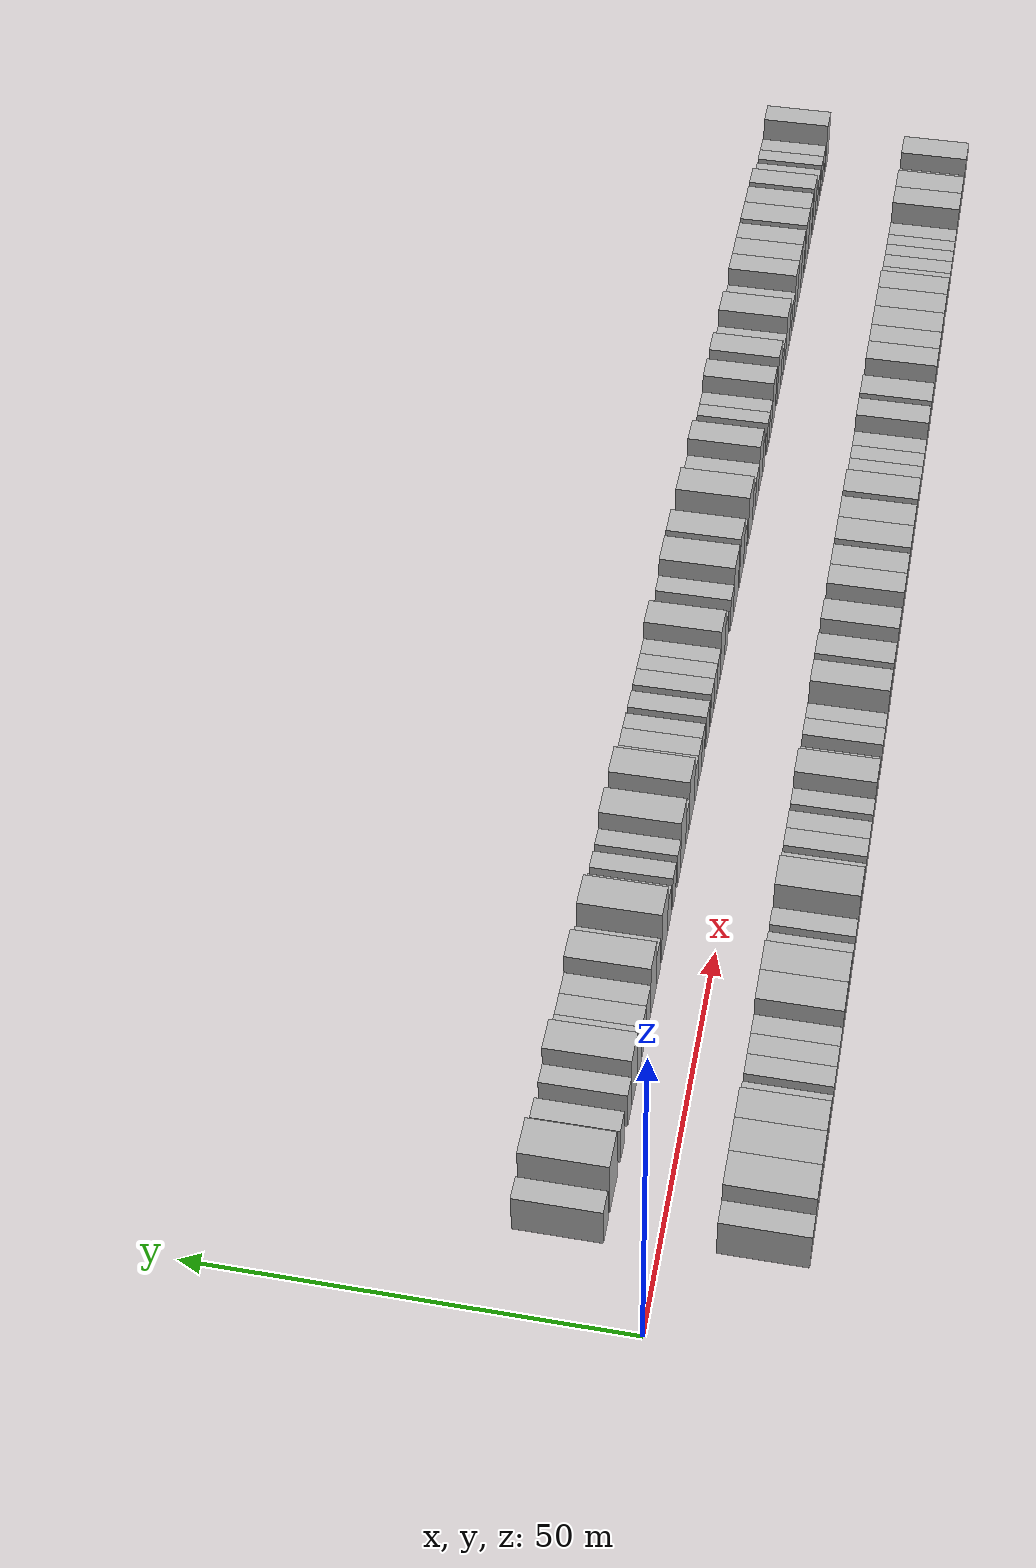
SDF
<sdf version="1.6">
 <world name="default">
  <scene>
   <sky><clouds><speed>12</speed></clouds></sky>
   <ambient>0.4 0.4 0.4 1</ambient>
   <background>0.7 0.7 0.7 1</background>
   <shadows>1</shadows>
  </scene>
  <gravity>0 0 -9.8066</gravity>
  <magnetic_field>6e-06 2.3e-05 -4.2e-05</magnetic_field>
  <physics default="0" name="default_physics" type="ode">
   <ode>
    <solver>
     <type>quick</type>
     <iters>10</iters>
     <sor>1.0</sor>
     <use_dynamic_moi_rescaling>0</use_dynamic_moi_rescaling>
    </solver>
    <constraints>
     <cfm>0</cfm>
     <erp>0.2</erp>
     <contact_max_correcting_vel>100</contact_max_correcting_vel>
     <contact_surface_layer>0.001</contact_surface_layer>
    </constraints>
   </ode>
   <max_step_size>0.004</max_step_size>
   <real_time_factor>1</real_time_factor>
   <real_time_update_rate>250</real_time_update_rate>
  </physics>
  <light name="sun" type="directional">
   <pose>0 0 10 0 0 0</pose>
   <diffuse>0.8 0.8 0.8 1</diffuse>
   <specular>0.2 0.2 0.2 1</specular>
   <attenuation>
    <range>1000</range>
    <constant>0.9</constant>
    <linear>0.01</linear>
    <quadratic>0.001</quadratic>
   </attenuation>
   <direction>-0.5 0.1 -0.9</direction>
  </light>
  <model name="building_1">
   <static>1</static>
   <pose>11.3619 11.0000 0 0.000000 0.000000 1.570796</pose>
   <link name="link">
    <pose>0 0 3.00 0 0 0</pose>
    <collision name="collision"><geometry><box><size>10.0000 2.7237 6.0000</size></box></geometry></collision>
    <visual name="visual">
     <cast_shadows>0</cast_shadows>
     <geometry><box><size>10.0000 2.7237 6.0000</size></box></geometry>
     <material>
      <script>
       <uri>model://HANNAS_wall/materials/scripts</uri>
       <uri>model://HANNAS_wall/materials/textures</uri>
       <name>vrc/HANNAS_wall</name>
      </script>
     </material>
    </visual>
   </link>
  </model>
  <model name="building_2">
   <static>1</static>
   <pose>15.9564 11.0000 0 0.000000 0.000000 1.570796</pose>
   <link name="link">
    <pose>0 0 4.50 0 0 0</pose>
    <collision name="collision"><geometry><box><size>10.0000 4.4653 9.0000</size></box></geometry></collision>
    <visual name="visual">
     <cast_shadows>0</cast_shadows>
     <geometry><box><size>10.0000 4.4653 9.0000</size></box></geometry>
     <material>
      <script>
       <uri>model://HANNAS_wall/materials/scripts</uri>
       <uri>model://HANNAS_wall/materials/textures</uri>
       <name>vrc/HANNAS_wall</name>
      </script>
     </material>
    </visual>
   </link>
  </model>
  <model name="building_3">
   <static>1</static>
   <pose>21.4835 11.0000 0 0.000000 0.000000 1.570796</pose>
   <link name="link">
    <pose>0 0 3.00 0 0 0</pose>
    <collision name="collision"><geometry><box><size>10.0000 2.5890 6.0000</size></box></geometry></collision>
    <visual name="visual">
     <cast_shadows>0</cast_shadows>
     <geometry><box><size>10.0000 2.5890 6.0000</size></box></geometry>
     <material>
      <script>
       <uri>model://HANNAS_wall/materials/scripts</uri>
       <uri>model://HANNAS_wall/materials/textures</uri>
       <name>vrc/HANNAS_wall</name>
      </script>
     </material>
    </visual>
   </link>
  </model>
  <model name="building_4">
   <static>1</static>
   <pose>26.0084 11.0000 0 0.000000 0.000000 1.570796</pose>
   <link name="link">
    <pose>0 0 3.00 0 0 0</pose>
    <collision name="collision"><geometry><box><size>10.0000 2.4608 6.0000</size></box></geometry></collision>
    <visual name="visual">
     <cast_shadows>0</cast_shadows>
     <geometry><box><size>10.0000 2.4608 6.0000</size></box></geometry>
     <material>
      <script>
       <uri>model://HANNAS_wall/materials/scripts</uri>
       <uri>model://HANNAS_wall/materials/textures</uri>
       <name>vrc/HANNAS_wall</name>
      </script>
     </material>
    </visual>
   </link>
  </model>
  <model name="building_5">
   <static>1</static>
   <pose>29.1895 11.0000 0 0.000000 0.000000 1.570796</pose>
   <link name="link">
    <pose>0 0 4.50 0 0 0</pose>
    <collision name="collision"><geometry><box><size>10.0000 3.9013 9.0000</size></box></geometry></collision>
    <visual name="visual">
     <cast_shadows>0</cast_shadows>
     <geometry><box><size>10.0000 3.9013 9.0000</size></box></geometry>
     <material>
      <script>
       <uri>model://HANNAS_wall/materials/scripts</uri>
       <uri>model://HANNAS_wall/materials/textures</uri>
       <name>vrc/HANNAS_wall</name>
      </script>
     </material>
    </visual>
   </link>
  </model>
  <model name="building_6">
   <static>1</static>
   <pose>32.5640 11.0000 0 0.000000 0.000000 1.570796</pose>
   <link name="link">
    <pose>0 0 3.00 0 0 0</pose>
    <collision name="collision"><geometry><box><size>10.0000 2.8478 6.0000</size></box></geometry></collision>
    <visual name="visual">
     <cast_shadows>0</cast_shadows>
     <geometry><box><size>10.0000 2.8478 6.0000</size></box></geometry>
     <material>
      <script>
       <uri>model://HANNAS_wall/materials/scripts</uri>
       <uri>model://HANNAS_wall/materials/textures</uri>
       <name>vrc/HANNAS_wall</name>
      </script>
     </material>
    </visual>
   </link>
  </model>
  <model name="building_7">
   <static>1</static>
   <pose>35.4418 11.0000 0 0.000000 0.000000 1.570796</pose>
   <link name="link">
    <pose>0 0 3.00 0 0 0</pose>
    <collision name="collision"><geometry><box><size>10.0000 2.9078 6.0000</size></box></geometry></collision>
    <visual name="visual">
     <cast_shadows>0</cast_shadows>
     <geometry><box><size>10.0000 2.9078 6.0000</size></box></geometry>
     <material>
      <script>
       <uri>model://HANNAS_wall/materials/scripts</uri>
       <uri>model://HANNAS_wall/materials/textures</uri>
       <name>vrc/HANNAS_wall</name>
      </script>
     </material>
    </visual>
   </link>
  </model>
  <model name="building_8">
   <static>1</static>
   <pose>38.3424 11.0000 0 0.000000 0.000000 1.570796</pose>
   <link name="link">
    <pose>0 0 3.00 0 0 0</pose>
    <collision name="collision"><geometry><box><size>10.0000 2.8935 6.0000</size></box></geometry></collision>
    <visual name="visual">
     <cast_shadows>0</cast_shadows>
     <geometry><box><size>10.0000 2.8935 6.0000</size></box></geometry>
     <material>
      <script>
       <uri>model://HANNAS_wall/materials/scripts</uri>
       <uri>model://HANNAS_wall/materials/textures</uri>
       <name>vrc/HANNAS_wall</name>
      </script>
     </material>
    </visual>
   </link>
  </model>
  <model name="building_9">
   <static>1</static>
   <pose>41.7459 11.0000 0 0.000000 0.000000 1.570796</pose>
   <link name="link">
    <pose>0 0 4.50 0 0 0</pose>
    <collision name="collision"><geometry><box><size>10.0000 3.9136 9.0000</size></box></geometry></collision>
    <visual name="visual">
     <cast_shadows>0</cast_shadows>
     <geometry><box><size>10.0000 3.9136 9.0000</size></box></geometry>
     <material>
      <script>
       <uri>model://HANNAS_wall/materials/scripts</uri>
       <uri>model://HANNAS_wall/materials/textures</uri>
       <name>vrc/HANNAS_wall</name>
      </script>
     </material>
    </visual>
   </link>
  </model>
  <model name="building_10">
   <static>1</static>
   <pose>45.0957 11.0000 0 0.000000 0.000000 1.570796</pose>
   <link name="link">
    <pose>0 0 3.00 0 0 0</pose>
    <collision name="collision"><geometry><box><size>10.0000 2.7859 6.0000</size></box></geometry></collision>
    <visual name="visual">
     <cast_shadows>0</cast_shadows>
     <geometry><box><size>10.0000 2.7859 6.0000</size></box></geometry>
     <material>
      <script>
       <uri>model://HANNAS_wall/materials/scripts</uri>
       <uri>model://HANNAS_wall/materials/textures</uri>
       <name>vrc/HANNAS_wall</name>
      </script>
     </material>
    </visual>
   </link>
  </model>
  <model name="building_11">
   <static>1</static>
   <pose>49.6018 11.0000 0 0.000000 0.000000 1.570796</pose>
   <link name="link">
    <pose>0 0 4.50 0 0 0</pose>
    <collision name="collision"><geometry><box><size>10.0000 4.2262 9.0000</size></box></geometry></collision>
    <visual name="visual">
     <cast_shadows>0</cast_shadows>
     <geometry><box><size>10.0000 4.2262 9.0000</size></box></geometry>
     <material>
      <script>
       <uri>model://HANNAS_wall/materials/scripts</uri>
       <uri>model://HANNAS_wall/materials/textures</uri>
       <name>vrc/HANNAS_wall</name>
      </script>
     </material>
    </visual>
   </link>
  </model>
  <model name="building_12">
   <static>1</static>
   <pose>52.9961 11.0000 0 0.000000 0.000000 1.570796</pose>
   <link name="link">
    <pose>0 0 3.00 0 0 0</pose>
    <collision name="collision"><geometry><box><size>10.0000 2.5625 6.0000</size></box></geometry></collision>
    <visual name="visual">
     <cast_shadows>0</cast_shadows>
     <geometry><box><size>10.0000 2.5625 6.0000</size></box></geometry>
     <material>
      <script>
       <uri>model://HANNAS_wall/materials/scripts</uri>
       <uri>model://HANNAS_wall/materials/textures</uri>
       <name>vrc/HANNAS_wall</name>
      </script>
     </material>
    </visual>
   </link>
  </model>
  <model name="building_13">
   <static>1</static>
   <pose>56.5271 11.0000 0 0.000000 0.000000 1.570796</pose>
   <link name="link">
    <pose>0 0 3.00 0 0 0</pose>
    <collision name="collision"><geometry><box><size>10.0000 2.4995 6.0000</size></box></geometry></collision>
    <visual name="visual">
     <cast_shadows>0</cast_shadows>
     <geometry><box><size>10.0000 2.4995 6.0000</size></box></geometry>
     <material>
      <script>
       <uri>model://HANNAS_wall/materials/scripts</uri>
       <uri>model://HANNAS_wall/materials/textures</uri>
       <name>vrc/HANNAS_wall</name>
      </script>
     </material>
    </visual>
   </link>
  </model>
  <model name="building_14">
   <static>1</static>
   <pose>60.0050 11.0000 0 0.000000 0.000000 1.570796</pose>
   <link name="link">
    <pose>0 0 3.00 0 0 0</pose>
    <collision name="collision"><geometry><box><size>10.0000 2.4562 6.0000</size></box></geometry></collision>
    <visual name="visual">
     <cast_shadows>0</cast_shadows>
     <geometry><box><size>10.0000 2.4562 6.0000</size></box></geometry>
     <material>
      <script>
       <uri>model://HANNAS_wall/materials/scripts</uri>
       <uri>model://HANNAS_wall/materials/textures</uri>
       <name>vrc/HANNAS_wall</name>
      </script>
     </material>
    </visual>
   </link>
  </model>
  <model name="building_15">
   <static>1</static>
   <pose>63.2275 11.0000 0 0.000000 0.000000 1.570796</pose>
   <link name="link">
    <pose>0 0 4.50 0 0 0</pose>
    <collision name="collision"><geometry><box><size>10.0000 3.9888 9.0000</size></box></geometry></collision>
    <visual name="visual">
     <cast_shadows>0</cast_shadows>
     <geometry><box><size>10.0000 3.9888 9.0000</size></box></geometry>
     <material>
      <script>
       <uri>model://HANNAS_wall/materials/scripts</uri>
       <uri>model://HANNAS_wall/materials/textures</uri>
       <name>vrc/HANNAS_wall</name>
      </script>
     </material>
    </visual>
   </link>
  </model>
  <model name="building_16">
   <static>1</static>
   <pose>66.4500 11.0000 0 0.000000 0.000000 1.570796</pose>
   <link name="link">
    <pose>0 0 3.00 0 0 0</pose>
    <collision name="collision"><geometry><box><size>10.0000 2.4563 6.0000</size></box></geometry></collision>
    <visual name="visual">
     <cast_shadows>0</cast_shadows>
     <geometry><box><size>10.0000 2.4563 6.0000</size></box></geometry>
     <material>
      <script>
       <uri>model://HANNAS_wall/materials/scripts</uri>
       <uri>model://HANNAS_wall/materials/textures</uri>
       <name>vrc/HANNAS_wall</name>
      </script>
     </material>
    </visual>
   </link>
  </model>
  <model name="building_17">
   <static>1</static>
   <pose>69.7121 11.0000 0 0.000000 0.000000 1.570796</pose>
   <link name="link">
    <pose>0 0 4.50 0 0 0</pose>
    <collision name="collision"><geometry><box><size>10.0000 4.0678 9.0000</size></box></geometry></collision>
    <visual name="visual">
     <cast_shadows>0</cast_shadows>
     <geometry><box><size>10.0000 4.0678 9.0000</size></box></geometry>
     <material>
      <script>
       <uri>model://HANNAS_wall/materials/scripts</uri>
       <uri>model://HANNAS_wall/materials/textures</uri>
       <name>vrc/HANNAS_wall</name>
      </script>
     </material>
    </visual>
   </link>
  </model>
  <model name="building_18">
   <static>1</static>
   <pose>73.2113 11.0000 0 0.000000 0.000000 1.570796</pose>
   <link name="link">
    <pose>0 0 3.00 0 0 0</pose>
    <collision name="collision"><geometry><box><size>10.0000 2.9305 6.0000</size></box></geometry></collision>
    <visual name="visual">
     <cast_shadows>0</cast_shadows>
     <geometry><box><size>10.0000 2.9305 6.0000</size></box></geometry>
     <material>
      <script>
       <uri>model://HANNAS_wall/materials/scripts</uri>
       <uri>model://HANNAS_wall/materials/textures</uri>
       <name>vrc/HANNAS_wall</name>
      </script>
     </material>
    </visual>
   </link>
  </model>
  <model name="building_19">
   <static>1</static>
   <pose>76.1501 11.0000 0 0.000000 0.000000 1.570796</pose>
   <link name="link">
    <pose>0 0 3.00 0 0 0</pose>
    <collision name="collision"><geometry><box><size>10.0000 2.9472 6.0000</size></box></geometry></collision>
    <visual name="visual">
     <cast_shadows>0</cast_shadows>
     <geometry><box><size>10.0000 2.9472 6.0000</size></box></geometry>
     <material>
      <script>
       <uri>model://HANNAS_wall/materials/scripts</uri>
       <uri>model://HANNAS_wall/materials/textures</uri>
       <name>vrc/HANNAS_wall</name>
      </script>
     </material>
    </visual>
   </link>
  </model>
  <model name="building_20">
   <static>1</static>
   <pose>78.8567 11.0000 0 0.000000 0.000000 1.570796</pose>
   <link name="link">
    <pose>0 0 3.00 0 0 0</pose>
    <collision name="collision"><geometry><box><size>10.0000 2.4658 6.0000</size></box></geometry></collision>
    <visual name="visual">
     <cast_shadows>0</cast_shadows>
     <geometry><box><size>10.0000 2.4658 6.0000</size></box></geometry>
     <material>
      <script>
       <uri>model://HANNAS_wall/materials/scripts</uri>
       <uri>model://HANNAS_wall/materials/textures</uri>
       <name>vrc/HANNAS_wall</name>
      </script>
     </material>
    </visual>
   </link>
  </model>
  <model name="building_21">
   <static>1</static>
   <pose>82.5169 11.0000 0 0.000000 0.000000 1.570796</pose>
   <link name="link">
    <pose>0 0 3.00 0 0 0</pose>
    <collision name="collision"><geometry><box><size>10.0000 2.8547 6.0000</size></box></geometry></collision>
    <visual name="visual">
     <cast_shadows>0</cast_shadows>
     <geometry><box><size>10.0000 2.8547 6.0000</size></box></geometry>
     <material>
      <script>
       <uri>model://HANNAS_wall/materials/scripts</uri>
       <uri>model://HANNAS_wall/materials/textures</uri>
       <name>vrc/HANNAS_wall</name>
      </script>
     </material>
    </visual>
   </link>
  </model>
  <model name="building_22">
   <static>1</static>
   <pose>86.3643 11.0000 0 0.000000 0.000000 1.570796</pose>
   <link name="link">
    <pose>0 0 3.00 0 0 0</pose>
    <collision name="collision"><geometry><box><size>10.0000 2.8400 6.0000</size></box></geometry></collision>
    <visual name="visual">
     <cast_shadows>0</cast_shadows>
     <geometry><box><size>10.0000 2.8400 6.0000</size></box></geometry>
     <material>
      <script>
       <uri>model://HANNAS_wall/materials/scripts</uri>
       <uri>model://HANNAS_wall/materials/textures</uri>
       <name>vrc/HANNAS_wall</name>
      </script>
     </material>
    </visual>
   </link>
  </model>
  <model name="building_23">
   <static>1</static>
   <pose>89.1174 11.0000 0 0.000000 0.000000 1.570796</pose>
   <link name="link">
    <pose>0 0 3.00 0 0 0</pose>
    <collision name="collision"><geometry><box><size>10.0000 2.6662 6.0000</size></box></geometry></collision>
    <visual name="visual">
     <cast_shadows>0</cast_shadows>
     <geometry><box><size>10.0000 2.6662 6.0000</size></box></geometry>
     <material>
      <script>
       <uri>model://HANNAS_wall/materials/scripts</uri>
       <uri>model://HANNAS_wall/materials/textures</uri>
       <name>vrc/HANNAS_wall</name>
      </script>
     </material>
    </visual>
   </link>
  </model>
  <model name="building_24">
   <static>1</static>
   <pose>91.7686 11.0000 0 0.000000 0.000000 1.570796</pose>
   <link name="link">
    <pose>0 0 3.00 0 0 0</pose>
    <collision name="collision"><geometry><box><size>10.0000 2.6361 6.0000</size></box></geometry></collision>
    <visual name="visual">
     <cast_shadows>0</cast_shadows>
     <geometry><box><size>10.0000 2.6361 6.0000</size></box></geometry>
     <material>
      <script>
       <uri>model://HANNAS_wall/materials/scripts</uri>
       <uri>model://HANNAS_wall/materials/textures</uri>
       <name>vrc/HANNAS_wall</name>
      </script>
     </material>
    </visual>
   </link>
  </model>
  <model name="building_25">
   <static>1</static>
   <pose>95.0623 11.0000 0 0.000000 0.000000 1.570796</pose>
   <link name="link">
    <pose>0 0 4.50 0 0 0</pose>
    <collision name="collision"><geometry><box><size>10.0000 3.9512 9.0000</size></box></geometry></collision>
    <visual name="visual">
     <cast_shadows>0</cast_shadows>
     <geometry><box><size>10.0000 3.9512 9.0000</size></box></geometry>
     <material>
      <script>
       <uri>model://HANNAS_wall/materials/scripts</uri>
       <uri>model://HANNAS_wall/materials/textures</uri>
       <name>vrc/HANNAS_wall</name>
      </script>
     </material>
    </visual>
   </link>
  </model>
  <model name="building_26">
   <static>1</static>
   <pose>98.4367 11.0000 0 0.000000 0.000000 1.570796</pose>
   <link name="link">
    <pose>0 0 3.00 0 0 0</pose>
    <collision name="collision"><geometry><box><size>10.0000 2.7976 6.0000</size></box></geometry></collision>
    <visual name="visual">
     <cast_shadows>0</cast_shadows>
     <geometry><box><size>10.0000 2.7976 6.0000</size></box></geometry>
     <material>
      <script>
       <uri>model://HANNAS_wall/materials/scripts</uri>
       <uri>model://HANNAS_wall/materials/textures</uri>
       <name>vrc/HANNAS_wall</name>
      </script>
     </material>
    </visual>
   </link>
  </model>
  <model name="building_27">
   <static>1</static>
   <pose>103.2614 11.0000 0 0.000000 0.000000 1.570796</pose>
   <link name="link">
    <pose>0 0 3.00 0 0 0</pose>
    <collision name="collision"><geometry><box><size>10.0000 2.8519 6.0000</size></box></geometry></collision>
    <visual name="visual">
     <cast_shadows>0</cast_shadows>
     <geometry><box><size>10.0000 2.8519 6.0000</size></box></geometry>
     <material>
      <script>
       <uri>model://HANNAS_wall/materials/scripts</uri>
       <uri>model://HANNAS_wall/materials/textures</uri>
       <name>vrc/HANNAS_wall</name>
      </script>
     </material>
    </visual>
   </link>
  </model>
  <model name="building_28">
   <static>1</static>
   <pose>106.9206 11.0000 0 0.000000 0.000000 1.570796</pose>
   <link name="link">
    <pose>0 0 4.50 0 0 0</pose>
    <collision name="collision"><geometry><box><size>10.0000 4.4664 9.0000</size></box></geometry></collision>
    <visual name="visual">
     <cast_shadows>0</cast_shadows>
     <geometry><box><size>10.0000 4.4664 9.0000</size></box></geometry>
     <material>
      <script>
       <uri>model://HANNAS_wall/materials/scripts</uri>
       <uri>model://HANNAS_wall/materials/textures</uri>
       <name>vrc/HANNAS_wall</name>
      </script>
     </material>
    </visual>
   </link>
  </model>
  <model name="building_29">
   <static>1</static>
   <pose>112.1940 11.0000 0 0.000000 0.000000 1.570796</pose>
   <link name="link">
    <pose>0 0 4.50 0 0 0</pose>
    <collision name="collision"><geometry><box><size>10.0000 4.0805 9.0000</size></box></geometry></collision>
    <visual name="visual">
     <cast_shadows>0</cast_shadows>
     <geometry><box><size>10.0000 4.0805 9.0000</size></box></geometry>
     <material>
      <script>
       <uri>model://HANNAS_wall/materials/scripts</uri>
       <uri>model://HANNAS_wall/materials/textures</uri>
       <name>vrc/HANNAS_wall</name>
      </script>
     </material>
    </visual>
   </link>
  </model>
  <model name="building_30">
   <static>1</static>
   <pose>115.7216 11.0000 0 0.000000 0.000000 1.570796</pose>
   <link name="link">
    <pose>0 0 3.00 0 0 0</pose>
    <collision name="collision"><geometry><box><size>10.0000 2.9746 6.0000</size></box></geometry></collision>
    <visual name="visual">
     <cast_shadows>0</cast_shadows>
     <geometry><box><size>10.0000 2.9746 6.0000</size></box></geometry>
     <material>
      <script>
       <uri>model://HANNAS_wall/materials/scripts</uri>
       <uri>model://HANNAS_wall/materials/textures</uri>
       <name>vrc/HANNAS_wall</name>
      </script>
     </material>
    </visual>
   </link>
  </model>
  <model name="building_31">
   <static>1</static>
   <pose>120.4012 11.0000 0 0.000000 0.000000 1.570796</pose>
   <link name="link">
    <pose>0 0 4.50 0 0 0</pose>
    <collision name="collision"><geometry><box><size>10.0000 4.3846 9.0000</size></box></geometry></collision>
    <visual name="visual">
     <cast_shadows>0</cast_shadows>
     <geometry><box><size>10.0000 4.3846 9.0000</size></box></geometry>
     <material>
      <script>
       <uri>model://HANNAS_wall/materials/scripts</uri>
       <uri>model://HANNAS_wall/materials/textures</uri>
       <name>vrc/HANNAS_wall</name>
      </script>
     </material>
    </visual>
   </link>
  </model>
  <model name="building_32">
   <static>1</static>
   <pose>124.0630 11.0000 0 0.000000 0.000000 1.570796</pose>
   <link name="link">
    <pose>0 0 3.00 0 0 0</pose>
    <collision name="collision"><geometry><box><size>10.0000 2.9389 6.0000</size></box></geometry></collision>
    <visual name="visual">
     <cast_shadows>0</cast_shadows>
     <geometry><box><size>10.0000 2.9389 6.0000</size></box></geometry>
     <material>
      <script>
       <uri>model://HANNAS_wall/materials/scripts</uri>
       <uri>model://HANNAS_wall/materials/textures</uri>
       <name>vrc/HANNAS_wall</name>
      </script>
     </material>
    </visual>
   </link>
  </model>
  <model name="building_33">
   <static>1</static>
   <pose>127.0050 11.0000 0 0.000000 0.000000 1.570796</pose>
   <link name="link">
    <pose>0 0 3.00 0 0 0</pose>
    <collision name="collision"><geometry><box><size>10.0000 2.9452 6.0000</size></box></geometry></collision>
    <visual name="visual">
     <cast_shadows>0</cast_shadows>
     <geometry><box><size>10.0000 2.9452 6.0000</size></box></geometry>
     <material>
      <script>
       <uri>model://HANNAS_wall/materials/scripts</uri>
       <uri>model://HANNAS_wall/materials/textures</uri>
       <name>vrc/HANNAS_wall</name>
      </script>
     </material>
    </visual>
   </link>
  </model>
  <model name="building_34">
   <static>1</static>
   <pose>130.4113 11.0000 0 0.000000 0.000000 1.570796</pose>
   <link name="link">
    <pose>0 0 4.50 0 0 0</pose>
    <collision name="collision"><geometry><box><size>10.0000 3.8673 9.0000</size></box></geometry></collision>
    <visual name="visual">
     <cast_shadows>0</cast_shadows>
     <geometry><box><size>10.0000 3.8673 9.0000</size></box></geometry>
     <material>
      <script>
       <uri>model://HANNAS_wall/materials/scripts</uri>
       <uri>model://HANNAS_wall/materials/textures</uri>
       <name>vrc/HANNAS_wall</name>
      </script>
     </material>
    </visual>
   </link>
  </model>
  <model name="building_35">
   <static>1</static>
   <pose>133.6094 11.0000 0 0.000000 0.000000 1.570796</pose>
   <link name="link">
    <pose>0 0 3.00 0 0 0</pose>
    <collision name="collision"><geometry><box><size>10.0000 2.5289 6.0000</size></box></geometry></collision>
    <visual name="visual">
     <cast_shadows>0</cast_shadows>
     <geometry><box><size>10.0000 2.5289 6.0000</size></box></geometry>
     <material>
      <script>
       <uri>model://HANNAS_wall/materials/scripts</uri>
       <uri>model://HANNAS_wall/materials/textures</uri>
       <name>vrc/HANNAS_wall</name>
      </script>
     </material>
    </visual>
   </link>
  </model>
  <model name="building_36">
   <static>1</static>
   <pose>138.0905 11.0000 0 0.000000 0.000000 1.570796</pose>
   <link name="link">
    <pose>0 0 3.00 0 0 0</pose>
    <collision name="collision"><geometry><box><size>10.0000 2.4332 6.0000</size></box></geometry></collision>
    <visual name="visual">
     <cast_shadows>0</cast_shadows>
     <geometry><box><size>10.0000 2.4332 6.0000</size></box></geometry>
     <material>
      <script>
       <uri>model://HANNAS_wall/materials/scripts</uri>
       <uri>model://HANNAS_wall/materials/textures</uri>
       <name>vrc/HANNAS_wall</name>
      </script>
     </material>
    </visual>
   </link>
  </model>
  <model name="building_37">
   <static>1</static>
   <pose>140.6060 11.0000 0 0.000000 0.000000 1.570796</pose>
   <link name="link">
    <pose>0 0 3.00 0 0 0</pose>
    <collision name="collision"><geometry><box><size>10.0000 2.5978 6.0000</size></box></geometry></collision>
    <visual name="visual">
     <cast_shadows>0</cast_shadows>
     <geometry><box><size>10.0000 2.5978 6.0000</size></box></geometry>
     <material>
      <script>
       <uri>model://HANNAS_wall/materials/scripts</uri>
       <uri>model://HANNAS_wall/materials/textures</uri>
       <name>vrc/HANNAS_wall</name>
      </script>
     </material>
    </visual>
   </link>
  </model>
  <model name="building_38">
   <static>1</static>
   <pose>143.7648 11.0000 0 0.000000 0.000000 1.570796</pose>
   <link name="link">
    <pose>0 0 4.50 0 0 0</pose>
    <collision name="collision"><geometry><box><size>10.0000 3.7199 9.0000</size></box></geometry></collision>
    <visual name="visual">
     <cast_shadows>0</cast_shadows>
     <geometry><box><size>10.0000 3.7199 9.0000</size></box></geometry>
     <material>
      <script>
       <uri>model://HANNAS_wall/materials/scripts</uri>
       <uri>model://HANNAS_wall/materials/textures</uri>
       <name>vrc/HANNAS_wall</name>
      </script>
     </material>
    </visual>
   </link>
  </model>
  <model name="building_39">
   <static>1</static>
   <pose>149.5519 11.0000 0 0.000000 0.000000 1.570796</pose>
   <link name="link">
    <pose>0 0 4.50 0 0 0</pose>
    <collision name="collision"><geometry><box><size>10.0000 3.8543 9.0000</size></box></geometry></collision>
    <visual name="visual">
     <cast_shadows>0</cast_shadows>
     <geometry><box><size>10.0000 3.8543 9.0000</size></box></geometry>
     <material>
      <script>
       <uri>model://HANNAS_wall/materials/scripts</uri>
       <uri>model://HANNAS_wall/materials/textures</uri>
       <name>vrc/HANNAS_wall</name>
      </script>
     </material>
    </visual>
   </link>
  </model>
  <model name="building_40">
   <static>1</static>
   <pose>152.8658 11.0000 0 0.000000 0.000000 1.570796</pose>
   <link name="link">
    <pose>0 0 3.00 0 0 0</pose>
    <collision name="collision"><geometry><box><size>10.0000 2.7734 6.0000</size></box></geometry></collision>
    <visual name="visual">
     <cast_shadows>0</cast_shadows>
     <geometry><box><size>10.0000 2.7734 6.0000</size></box></geometry>
     <material>
      <script>
       <uri>model://HANNAS_wall/materials/scripts</uri>
       <uri>model://HANNAS_wall/materials/textures</uri>
       <name>vrc/HANNAS_wall</name>
      </script>
     </material>
    </visual>
   </link>
  </model>
  <model name="building_41">
   <static>1</static>
   <pose>155.4579 11.0000 0 0.000000 0.000000 1.570796</pose>
   <link name="link">
    <pose>0 0 3.00 0 0 0</pose>
    <collision name="collision"><geometry><box><size>10.0000 2.4107 6.0000</size></box></geometry></collision>
    <visual name="visual">
     <cast_shadows>0</cast_shadows>
     <geometry><box><size>10.0000 2.4107 6.0000</size></box></geometry>
     <material>
      <script>
       <uri>model://HANNAS_wall/materials/scripts</uri>
       <uri>model://HANNAS_wall/materials/textures</uri>
       <name>vrc/HANNAS_wall</name>
      </script>
     </material>
    </visual>
   </link>
  </model>
  <model name="building_42">
   <static>1</static>
   <pose>158.8266 11.0000 0 0.000000 0.000000 1.570796</pose>
   <link name="link">
    <pose>0 0 4.50 0 0 0</pose>
    <collision name="collision"><geometry><box><size>10.0000 4.3266 9.0000</size></box></geometry></collision>
    <visual name="visual">
     <cast_shadows>0</cast_shadows>
     <geometry><box><size>10.0000 4.3266 9.0000</size></box></geometry>
     <material>
      <script>
       <uri>model://HANNAS_wall/materials/scripts</uri>
       <uri>model://HANNAS_wall/materials/textures</uri>
       <name>vrc/HANNAS_wall</name>
      </script>
     </material>
    </visual>
   </link>
  </model>
  <model name="building_43">
   <static>1</static>
   <pose>162.2011 11.0000 0 0.000000 0.000000 1.570796</pose>
   <link name="link">
    <pose>0 0 3.00 0 0 0</pose>
    <collision name="collision"><geometry><box><size>10.0000 2.4226 6.0000</size></box></geometry></collision>
    <visual name="visual">
     <cast_shadows>0</cast_shadows>
     <geometry><box><size>10.0000 2.4226 6.0000</size></box></geometry>
     <material>
      <script>
       <uri>model://HANNAS_wall/materials/scripts</uri>
       <uri>model://HANNAS_wall/materials/textures</uri>
       <name>vrc/HANNAS_wall</name>
      </script>
     </material>
    </visual>
   </link>
  </model>
  <model name="building_44">
   <static>1</static>
   <pose>164.8834 11.0000 0 0.000000 0.000000 1.570796</pose>
   <link name="link">
    <pose>0 0 3.00 0 0 0</pose>
    <collision name="collision"><geometry><box><size>10.0000 2.9419 6.0000</size></box></geometry></collision>
    <visual name="visual">
     <cast_shadows>0</cast_shadows>
     <geometry><box><size>10.0000 2.9419 6.0000</size></box></geometry>
     <material>
      <script>
       <uri>model://HANNAS_wall/materials/scripts</uri>
       <uri>model://HANNAS_wall/materials/textures</uri>
       <name>vrc/HANNAS_wall</name>
      </script>
     </material>
    </visual>
   </link>
  </model>
  <model name="building_45">
   <static>1</static>
   <pose>168.1910 11.0000 0 0.000000 0.000000 1.570796</pose>
   <link name="link">
    <pose>0 0 4.50 0 0 0</pose>
    <collision name="collision"><geometry><box><size>10.0000 3.6733 9.0000</size></box></geometry></collision>
    <visual name="visual">
     <cast_shadows>0</cast_shadows>
     <geometry><box><size>10.0000 3.6733 9.0000</size></box></geometry>
     <material>
      <script>
       <uri>model://HANNAS_wall/materials/scripts</uri>
       <uri>model://HANNAS_wall/materials/textures</uri>
       <name>vrc/HANNAS_wall</name>
      </script>
     </material>
    </visual>
   </link>
  </model>
  <model name="building_46">
   <static>1</static>
   <pose>171.9816 11.0000 0 0.000000 0.000000 1.570796</pose>
   <link name="link">
    <pose>0 0 4.50 0 0 0</pose>
    <collision name="collision"><geometry><box><size>10.0000 3.9079 9.0000</size></box></geometry></collision>
    <visual name="visual">
     <cast_shadows>0</cast_shadows>
     <geometry><box><size>10.0000 3.9079 9.0000</size></box></geometry>
     <material>
      <script>
       <uri>model://HANNAS_wall/materials/scripts</uri>
       <uri>model://HANNAS_wall/materials/textures</uri>
       <name>vrc/HANNAS_wall</name>
      </script>
     </material>
    </visual>
   </link>
  </model>
  <model name="building_47">
   <static>1</static>
   <pose>175.7639 11.0000 0 0.000000 0.000000 1.570796</pose>
   <link name="link">
    <pose>0 0 4.50 0 0 0</pose>
    <collision name="collision"><geometry><box><size>10.0000 3.6567 9.0000</size></box></geometry></collision>
    <visual name="visual">
     <cast_shadows>0</cast_shadows>
     <geometry><box><size>10.0000 3.6567 9.0000</size></box></geometry>
     <material>
      <script>
       <uri>model://HANNAS_wall/materials/scripts</uri>
       <uri>model://HANNAS_wall/materials/textures</uri>
       <name>vrc/HANNAS_wall</name>
      </script>
     </material>
    </visual>
   </link>
  </model>
  <model name="building_48">
   <static>1</static>
   <pose>180.7268 11.0000 0 0.000000 0.000000 1.570796</pose>
   <link name="link">
    <pose>0 0 4.50 0 0 0</pose>
    <collision name="collision"><geometry><box><size>10.0000 4.2690 9.0000</size></box></geometry></collision>
    <visual name="visual">
     <cast_shadows>0</cast_shadows>
     <geometry><box><size>10.0000 4.2690 9.0000</size></box></geometry>
     <material>
      <script>
       <uri>model://HANNAS_wall/materials/scripts</uri>
       <uri>model://HANNAS_wall/materials/textures</uri>
       <name>vrc/HANNAS_wall</name>
      </script>
     </material>
    </visual>
   </link>
  </model>
  <model name="building_49">
   <static>1</static>
   <pose>184.8466 11.0000 0 0.000000 0.000000 1.570796</pose>
   <link name="link">
    <pose>0 0 4.50 0 0 0</pose>
    <collision name="collision"><geometry><box><size>10.0000 3.9706 9.0000</size></box></geometry></collision>
    <visual name="visual">
     <cast_shadows>0</cast_shadows>
     <geometry><box><size>10.0000 3.9706 9.0000</size></box></geometry>
     <material>
      <script>
       <uri>model://HANNAS_wall/materials/scripts</uri>
       <uri>model://HANNAS_wall/materials/textures</uri>
       <name>vrc/HANNAS_wall</name>
      </script>
     </material>
    </visual>
   </link>
  </model>
  <model name="building_50">
   <static>1</static>
   <pose>189.6400 11.0000 0 0.000000 0.000000 1.570796</pose>
   <link name="link">
    <pose>0 0 4.50 0 0 0</pose>
    <collision name="collision"><geometry><box><size>10.0000 3.6162 9.0000</size></box></geometry></collision>
    <visual name="visual">
     <cast_shadows>0</cast_shadows>
     <geometry><box><size>10.0000 3.6162 9.0000</size></box></geometry>
     <material>
      <script>
       <uri>model://HANNAS_wall/materials/scripts</uri>
       <uri>model://HANNAS_wall/materials/textures</uri>
       <name>vrc/HANNAS_wall</name>
      </script>
     </material>
    </visual>
   </link>
  </model>
  <model name="building_51">
   <static>1</static>
   <pose>192.8970 11.0000 0 0.000000 0.000000 1.570796</pose>
   <link name="link">
    <pose>0 0 3.00 0 0 0</pose>
    <collision name="collision"><geometry><box><size>10.0000 2.8980 6.0000</size></box></geometry></collision>
    <visual name="visual">
     <cast_shadows>0</cast_shadows>
     <geometry><box><size>10.0000 2.8980 6.0000</size></box></geometry>
     <material>
      <script>
       <uri>model://HANNAS_wall/materials/scripts</uri>
       <uri>model://HANNAS_wall/materials/textures</uri>
       <name>vrc/HANNAS_wall</name>
      </script>
     </material>
    </visual>
   </link>
  </model>
  <model name="building_52">
   <static>1</static>
   <pose>195.7390 11.0000 0 0.000000 0.000000 1.570796</pose>
   <link name="link">
    <pose>0 0 3.00 0 0 0</pose>
    <collision name="collision"><geometry><box><size>10.0000 2.7860 6.0000</size></box></geometry></collision>
    <visual name="visual">
     <cast_shadows>0</cast_shadows>
     <geometry><box><size>10.0000 2.7860 6.0000</size></box></geometry>
     <material>
      <script>
       <uri>model://HANNAS_wall/materials/scripts</uri>
       <uri>model://HANNAS_wall/materials/textures</uri>
       <name>vrc/HANNAS_wall</name>
      </script>
     </material>
    </visual>
   </link>
  </model>
  <model name="building_53">
   <static>1</static>
   <pose>199.3828 11.0000 0 0.000000 0.000000 1.570796</pose>
   <link name="link">
    <pose>0 0 3.00 0 0 0</pose>
    <collision name="collision"><geometry><box><size>10.0000 2.5016 6.0000</size></box></geometry></collision>
    <visual name="visual">
     <cast_shadows>0</cast_shadows>
     <geometry><box><size>10.0000 2.5016 6.0000</size></box></geometry>
     <material>
      <script>
       <uri>model://HANNAS_wall/materials/scripts</uri>
       <uri>model://HANNAS_wall/materials/textures</uri>
       <name>vrc/HANNAS_wall</name>
      </script>
     </material>
    </visual>
   </link>
  </model>
  <model name="building_54">
   <static>1</static>
   <pose>202.0715 11.0000 0 0.000000 0.000000 1.570796</pose>
   <link name="link">
    <pose>0 0 3.00 0 0 0</pose>
    <collision name="collision"><geometry><box><size>10.0000 2.8758 6.0000</size></box></geometry></collision>
    <visual name="visual">
     <cast_shadows>0</cast_shadows>
     <geometry><box><size>10.0000 2.8758 6.0000</size></box></geometry>
     <material>
      <script>
       <uri>model://HANNAS_wall/materials/scripts</uri>
       <uri>model://HANNAS_wall/materials/textures</uri>
       <name>vrc/HANNAS_wall</name>
      </script>
     </material>
    </visual>
   </link>
  </model>
  <model name="building_55">
   <static>1</static>
   <pose>206.4218 11.0000 0 0.000000 0.000000 1.570796</pose>
   <link name="link">
    <pose>0 0 4.50 0 0 0</pose>
    <collision name="collision"><geometry><box><size>10.0000 3.8250 9.0000</size></box></geometry></collision>
    <visual name="visual">
     <cast_shadows>0</cast_shadows>
     <geometry><box><size>10.0000 3.8250 9.0000</size></box></geometry>
     <material>
      <script>
       <uri>model://HANNAS_wall/materials/scripts</uri>
       <uri>model://HANNAS_wall/materials/textures</uri>
       <name>vrc/HANNAS_wall</name>
      </script>
     </material>
    </visual>
   </link>
  </model>
  <model name="building_56">
   <static>1</static>
   <pose>12.4048 -11.0000 0 0.000000 0.000000 1.570796</pose>
   <link name="link">
    <pose>0 0 3.00 0 0 0</pose>
    <collision name="collision"><geometry><box><size>10.0000 2.8097 6.0000</size></box></geometry></collision>
    <visual name="visual">
     <cast_shadows>0</cast_shadows>
     <geometry><box><size>10.0000 2.8097 6.0000</size></box></geometry>
     <material>
      <script>
       <uri>model://HANNAS_wall/materials/scripts</uri>
       <uri>model://HANNAS_wall/materials/textures</uri>
       <name>vrc/HANNAS_wall</name>
      </script>
     </material>
    </visual>
   </link>
  </model>
  <model name="building_57">
   <static>1</static>
   <pose>15.9327 -11.0000 0 0.000000 0.000000 1.570796</pose>
   <link name="link">
    <pose>0 0 4.50 0 0 0</pose>
    <collision name="collision"><geometry><box><size>10.0000 4.2461 9.0000</size></box></geometry></collision>
    <visual name="visual">
     <cast_shadows>0</cast_shadows>
     <geometry><box><size>10.0000 4.2461 9.0000</size></box></geometry>
     <material>
      <script>
       <uri>model://HANNAS_wall/materials/scripts</uri>
       <uri>model://HANNAS_wall/materials/textures</uri>
       <name>vrc/HANNAS_wall</name>
      </script>
     </material>
    </visual>
   </link>
  </model>
  <model name="building_58">
   <static>1</static>
   <pose>20.1625 -11.0000 0 0.000000 0.000000 1.570796</pose>
   <link name="link">
    <pose>0 0 4.50 0 0 0</pose>
    <collision name="collision"><geometry><box><size>10.0000 4.2135 9.0000</size></box></geometry></collision>
    <visual name="visual">
     <cast_shadows>0</cast_shadows>
     <geometry><box><size>10.0000 4.2135 9.0000</size></box></geometry>
     <material>
      <script>
       <uri>model://HANNAS_wall/materials/scripts</uri>
       <uri>model://HANNAS_wall/materials/textures</uri>
       <name>vrc/HANNAS_wall</name>
      </script>
     </material>
    </visual>
   </link>
  </model>
  <model name="building_59">
   <static>1</static>
   <pose>24.1878 -11.0000 0 0.000000 0.000000 1.570796</pose>
   <link name="link">
    <pose>0 0 4.50 0 0 0</pose>
    <collision name="collision"><geometry><box><size>10.0000 3.8370 9.0000</size></box></geometry></collision>
    <visual name="visual">
     <cast_shadows>0</cast_shadows>
     <geometry><box><size>10.0000 3.8370 9.0000</size></box></geometry>
     <material>
      <script>
       <uri>model://HANNAS_wall/materials/scripts</uri>
       <uri>model://HANNAS_wall/materials/textures</uri>
       <name>vrc/HANNAS_wall</name>
      </script>
     </material>
    </visual>
   </link>
  </model>
  <model name="building_60">
   <static>1</static>
   <pose>27.5183 -11.0000 0 0.000000 0.000000 1.570796</pose>
   <link name="link">
    <pose>0 0 3.00 0 0 0</pose>
    <collision name="collision"><geometry><box><size>10.0000 2.8242 6.0000</size></box></geometry></collision>
    <visual name="visual">
     <cast_shadows>0</cast_shadows>
     <geometry><box><size>10.0000 2.8242 6.0000</size></box></geometry>
     <material>
      <script>
       <uri>model://HANNAS_wall/materials/scripts</uri>
       <uri>model://HANNAS_wall/materials/textures</uri>
       <name>vrc/HANNAS_wall</name>
      </script>
     </material>
    </visual>
   </link>
  </model>
  <model name="building_61">
   <static>1</static>
   <pose>31.2732 -11.0000 0 0.000000 0.000000 1.570796</pose>
   <link name="link">
    <pose>0 0 3.00 0 0 0</pose>
    <collision name="collision"><geometry><box><size>10.0000 2.6855 6.0000</size></box></geometry></collision>
    <visual name="visual">
     <cast_shadows>0</cast_shadows>
     <geometry><box><size>10.0000 2.6855 6.0000</size></box></geometry>
     <material>
      <script>
       <uri>model://HANNAS_wall/materials/scripts</uri>
       <uri>model://HANNAS_wall/materials/textures</uri>
       <name>vrc/HANNAS_wall</name>
      </script>
     </material>
    </visual>
   </link>
  </model>
  <model name="building_62">
   <static>1</static>
   <pose>33.9993 -11.0000 0 0.000000 0.000000 1.570796</pose>
   <link name="link">
    <pose>0 0 3.00 0 0 0</pose>
    <collision name="collision"><geometry><box><size>10.0000 2.7667 6.0000</size></box></geometry></collision>
    <visual name="visual">
     <cast_shadows>0</cast_shadows>
     <geometry><box><size>10.0000 2.7667 6.0000</size></box></geometry>
     <material>
      <script>
       <uri>model://HANNAS_wall/materials/scripts</uri>
       <uri>model://HANNAS_wall/materials/textures</uri>
       <name>vrc/HANNAS_wall</name>
      </script>
     </material>
    </visual>
   </link>
  </model>
  <model name="building_63">
   <static>1</static>
   <pose>36.6693 -11.0000 0 0.000000 0.000000 1.570796</pose>
   <link name="link">
    <pose>0 0 3.00 0 0 0</pose>
    <collision name="collision"><geometry><box><size>10.0000 2.5733 6.0000</size></box></geometry></collision>
    <visual name="visual">
     <cast_shadows>0</cast_shadows>
     <geometry><box><size>10.0000 2.5733 6.0000</size></box></geometry>
     <material>
      <script>
       <uri>model://HANNAS_wall/materials/scripts</uri>
       <uri>model://HANNAS_wall/materials/textures</uri>
       <name>vrc/HANNAS_wall</name>
      </script>
     </material>
    </visual>
   </link>
  </model>
  <model name="building_64">
   <static>1</static>
   <pose>39.9777 -11.0000 0 0.000000 0.000000 1.570796</pose>
   <link name="link">
    <pose>0 0 4.50 0 0 0</pose>
    <collision name="collision"><geometry><box><size>10.0000 4.0435 9.0000</size></box></geometry></collision>
    <visual name="visual">
     <cast_shadows>0</cast_shadows>
     <geometry><box><size>10.0000 4.0435 9.0000</size></box></geometry>
     <material>
      <script>
       <uri>model://HANNAS_wall/materials/scripts</uri>
       <uri>model://HANNAS_wall/materials/textures</uri>
       <name>vrc/HANNAS_wall</name>
      </script>
     </material>
    </visual>
   </link>
  </model>
  <model name="building_65">
   <static>1</static>
   <pose>44.0484 -11.0000 0 0.000000 0.000000 1.570796</pose>
   <link name="link">
    <pose>0 0 4.50 0 0 0</pose>
    <collision name="collision"><geometry><box><size>10.0000 4.0979 9.0000</size></box></geometry></collision>
    <visual name="visual">
     <cast_shadows>0</cast_shadows>
     <geometry><box><size>10.0000 4.0979 9.0000</size></box></geometry>
     <material>
      <script>
       <uri>model://HANNAS_wall/materials/scripts</uri>
       <uri>model://HANNAS_wall/materials/textures</uri>
       <name>vrc/HANNAS_wall</name>
      </script>
     </material>
    </visual>
   </link>
  </model>
  <model name="building_66">
   <static>1</static>
   <pose>48.3936 -11.0000 0 0.000000 0.000000 1.570796</pose>
   <link name="link">
    <pose>0 0 3.00 0 0 0</pose>
    <collision name="collision"><geometry><box><size>10.0000 2.5927 6.0000</size></box></geometry></collision>
    <visual name="visual">
     <cast_shadows>0</cast_shadows>
     <geometry><box><size>10.0000 2.5927 6.0000</size></box></geometry>
     <material>
      <script>
       <uri>model://HANNAS_wall/materials/scripts</uri>
       <uri>model://HANNAS_wall/materials/textures</uri>
       <name>vrc/HANNAS_wall</name>
      </script>
     </material>
    </visual>
   </link>
  </model>
  <model name="building_67">
   <static>1</static>
   <pose>51.9815 -11.0000 0 0.000000 0.000000 1.570796</pose>
   <link name="link">
    <pose>0 0 3.00 0 0 0</pose>
    <collision name="collision"><geometry><box><size>10.0000 2.5831 6.0000</size></box></geometry></collision>
    <visual name="visual">
     <cast_shadows>0</cast_shadows>
     <geometry><box><size>10.0000 2.5831 6.0000</size></box></geometry>
     <material>
      <script>
       <uri>model://HANNAS_wall/materials/scripts</uri>
       <uri>model://HANNAS_wall/materials/textures</uri>
       <name>vrc/HANNAS_wall</name>
      </script>
     </material>
    </visual>
   </link>
  </model>
  <model name="building_68">
   <static>1</static>
   <pose>56.4591 -11.0000 0 0.000000 0.000000 1.570796</pose>
   <link name="link">
    <pose>0 0 4.50 0 0 0</pose>
    <collision name="collision"><geometry><box><size>10.0000 4.3722 9.0000</size></box></geometry></collision>
    <visual name="visual">
     <cast_shadows>0</cast_shadows>
     <geometry><box><size>10.0000 4.3722 9.0000</size></box></geometry>
     <material>
      <script>
       <uri>model://HANNAS_wall/materials/scripts</uri>
       <uri>model://HANNAS_wall/materials/textures</uri>
       <name>vrc/HANNAS_wall</name>
      </script>
     </material>
    </visual>
   </link>
  </model>
  <model name="building_69">
   <static>1</static>
   <pose>60.1402 -11.0000 0 0.000000 0.000000 1.570796</pose>
   <link name="link">
    <pose>0 0 3.00 0 0 0</pose>
    <collision name="collision"><geometry><box><size>10.0000 2.9900 6.0000</size></box></geometry></collision>
    <visual name="visual">
     <cast_shadows>0</cast_shadows>
     <geometry><box><size>10.0000 2.9900 6.0000</size></box></geometry>
     <material>
      <script>
       <uri>model://HANNAS_wall/materials/scripts</uri>
       <uri>model://HANNAS_wall/materials/textures</uri>
       <name>vrc/HANNAS_wall</name>
      </script>
     </material>
    </visual>
   </link>
  </model>
  <model name="building_70">
   <static>1</static>
   <pose>64.0206 -11.0000 0 0.000000 0.000000 1.570796</pose>
   <link name="link">
    <pose>0 0 3.00 0 0 0</pose>
    <collision name="collision"><geometry><box><size>10.0000 2.7708 6.0000</size></box></geometry></collision>
    <visual name="visual">
     <cast_shadows>0</cast_shadows>
     <geometry><box><size>10.0000 2.7708 6.0000</size></box></geometry>
     <material>
      <script>
       <uri>model://HANNAS_wall/materials/scripts</uri>
       <uri>model://HANNAS_wall/materials/textures</uri>
       <name>vrc/HANNAS_wall</name>
      </script>
     </material>
    </visual>
   </link>
  </model>
  <model name="building_71">
   <static>1</static>
   <pose>66.7695 -11.0000 0 0.000000 0.000000 1.570796</pose>
   <link name="link">
    <pose>0 0 3.00 0 0 0</pose>
    <collision name="collision"><geometry><box><size>10.0000 2.7269 6.0000</size></box></geometry></collision>
    <visual name="visual">
     <cast_shadows>0</cast_shadows>
     <geometry><box><size>10.0000 2.7269 6.0000</size></box></geometry>
     <material>
      <script>
       <uri>model://HANNAS_wall/materials/scripts</uri>
       <uri>model://HANNAS_wall/materials/textures</uri>
       <name>vrc/HANNAS_wall</name>
      </script>
     </material>
    </visual>
   </link>
  </model>
  <model name="building_72">
   <static>1</static>
   <pose>70.4110 -11.0000 0 0.000000 0.000000 1.570796</pose>
   <link name="link">
    <pose>0 0 3.00 0 0 0</pose>
    <collision name="collision"><geometry><box><size>10.0000 2.5562 6.0000</size></box></geometry></collision>
    <visual name="visual">
     <cast_shadows>0</cast_shadows>
     <geometry><box><size>10.0000 2.5562 6.0000</size></box></geometry>
     <material>
      <script>
       <uri>model://HANNAS_wall/materials/scripts</uri>
       <uri>model://HANNAS_wall/materials/textures</uri>
       <name>vrc/HANNAS_wall</name>
      </script>
     </material>
    </visual>
   </link>
  </model>
  <model name="building_73">
   <static>1</static>
   <pose>73.6029 -11.0000 0 0.000000 0.000000 1.570796</pose>
   <link name="link">
    <pose>0 0 4.50 0 0 0</pose>
    <collision name="collision"><geometry><box><size>10.0000 3.8276 9.0000</size></box></geometry></collision>
    <visual name="visual">
     <cast_shadows>0</cast_shadows>
     <geometry><box><size>10.0000 3.8276 9.0000</size></box></geometry>
     <material>
      <script>
       <uri>model://HANNAS_wall/materials/scripts</uri>
       <uri>model://HANNAS_wall/materials/textures</uri>
       <name>vrc/HANNAS_wall</name>
      </script>
     </material>
    </visual>
   </link>
  </model>
  <model name="building_74">
   <static>1</static>
   <pose>76.9932 -11.0000 0 0.000000 0.000000 1.570796</pose>
   <link name="link">
    <pose>0 0 3.00 0 0 0</pose>
    <collision name="collision"><geometry><box><size>10.0000 2.9531 6.0000</size></box></geometry></collision>
    <visual name="visual">
     <cast_shadows>0</cast_shadows>
     <geometry><box><size>10.0000 2.9531 6.0000</size></box></geometry>
     <material>
      <script>
       <uri>model://HANNAS_wall/materials/scripts</uri>
       <uri>model://HANNAS_wall/materials/textures</uri>
       <name>vrc/HANNAS_wall</name>
      </script>
     </material>
    </visual>
   </link>
  </model>
  <model name="building_75">
   <static>1</static>
   <pose>81.8774 -11.0000 0 0.000000 0.000000 1.570796</pose>
   <link name="link">
    <pose>0 0 3.00 0 0 0</pose>
    <collision name="collision"><geometry><box><size>10.0000 2.8153 6.0000</size></box></geometry></collision>
    <visual name="visual">
     <cast_shadows>0</cast_shadows>
     <geometry><box><size>10.0000 2.8153 6.0000</size></box></geometry>
     <material>
      <script>
       <uri>model://HANNAS_wall/materials/scripts</uri>
       <uri>model://HANNAS_wall/materials/textures</uri>
       <name>vrc/HANNAS_wall</name>
      </script>
     </material>
    </visual>
   </link>
  </model>
  <model name="building_76">
   <static>1</static>
   <pose>84.5424 -11.0000 0 0.000000 0.000000 1.570796</pose>
   <link name="link">
    <pose>0 0 3.00 0 0 0</pose>
    <collision name="collision"><geometry><box><size>10.0000 2.5147 6.0000</size></box></geometry></collision>
    <visual name="visual">
     <cast_shadows>0</cast_shadows>
     <geometry><box><size>10.0000 2.5147 6.0000</size></box></geometry>
     <material>
      <script>
       <uri>model://HANNAS_wall/materials/scripts</uri>
       <uri>model://HANNAS_wall/materials/textures</uri>
       <name>vrc/HANNAS_wall</name>
      </script>
     </material>
    </visual>
   </link>
  </model>
  <model name="building_77">
   <static>1</static>
   <pose>88.6724 -11.0000 0 0.000000 0.000000 1.570796</pose>
   <link name="link">
    <pose>0 0 4.50 0 0 0</pose>
    <collision name="collision"><geometry><box><size>10.0000 3.7453 9.0000</size></box></geometry></collision>
    <visual name="visual">
     <cast_shadows>0</cast_shadows>
     <geometry><box><size>10.0000 3.7453 9.0000</size></box></geometry>
     <material>
      <script>
       <uri>model://HANNAS_wall/materials/scripts</uri>
       <uri>model://HANNAS_wall/materials/textures</uri>
       <name>vrc/HANNAS_wall</name>
      </script>
     </material>
    </visual>
   </link>
  </model>
  <model name="building_78">
   <static>1</static>
   <pose>93.3825 -11.0000 0 0.000000 0.000000 1.570796</pose>
   <link name="link">
    <pose>0 0 4.50 0 0 0</pose>
    <collision name="collision"><geometry><box><size>10.0000 3.6747 9.0000</size></box></geometry></collision>
    <visual name="visual">
     <cast_shadows>0</cast_shadows>
     <geometry><box><size>10.0000 3.6747 9.0000</size></box></geometry>
     <material>
      <script>
       <uri>model://HANNAS_wall/materials/scripts</uri>
       <uri>model://HANNAS_wall/materials/textures</uri>
       <name>vrc/HANNAS_wall</name>
      </script>
     </material>
    </visual>
   </link>
  </model>
  <model name="building_79">
   <static>1</static>
   <pose>96.4767 -11.0000 0 0.000000 0.000000 1.570796</pose>
   <link name="link">
    <pose>0 0 3.00 0 0 0</pose>
    <collision name="collision"><geometry><box><size>10.0000 2.5138 6.0000</size></box></geometry></collision>
    <visual name="visual">
     <cast_shadows>0</cast_shadows>
     <geometry><box><size>10.0000 2.5138 6.0000</size></box></geometry>
     <material>
      <script>
       <uri>model://HANNAS_wall/materials/scripts</uri>
       <uri>model://HANNAS_wall/materials/textures</uri>
       <name>vrc/HANNAS_wall</name>
      </script>
     </material>
    </visual>
   </link>
  </model>
  <model name="building_80">
   <static>1</static>
   <pose>99.5844 -11.0000 0 0.000000 0.000000 1.570796</pose>
   <link name="link">
    <pose>0 0 4.50 0 0 0</pose>
    <collision name="collision"><geometry><box><size>10.0000 3.7017 9.0000</size></box></geometry></collision>
    <visual name="visual">
     <cast_shadows>0</cast_shadows>
     <geometry><box><size>10.0000 3.7017 9.0000</size></box></geometry>
     <material>
      <script>
       <uri>model://HANNAS_wall/materials/scripts</uri>
       <uri>model://HANNAS_wall/materials/textures</uri>
       <name>vrc/HANNAS_wall</name>
      </script>
     </material>
    </visual>
   </link>
  </model>
  <model name="building_81">
   <static>1</static>
   <pose>102.8173 -11.0000 0 0.000000 0.000000 1.570796</pose>
   <link name="link">
    <pose>0 0 3.00 0 0 0</pose>
    <collision name="collision"><geometry><box><size>10.0000 2.7641 6.0000</size></box></geometry></collision>
    <visual name="visual">
     <cast_shadows>0</cast_shadows>
     <geometry><box><size>10.0000 2.7641 6.0000</size></box></geometry>
     <material>
      <script>
       <uri>model://HANNAS_wall/materials/scripts</uri>
       <uri>model://HANNAS_wall/materials/textures</uri>
       <name>vrc/HANNAS_wall</name>
      </script>
     </material>
    </visual>
   </link>
  </model>
  <model name="building_82">
   <static>1</static>
   <pose>106.0073 -11.0000 0 0.000000 0.000000 1.570796</pose>
   <link name="link">
    <pose>0 0 4.50 0 0 0</pose>
    <collision name="collision"><geometry><box><size>10.0000 3.6158 9.0000</size></box></geometry></collision>
    <visual name="visual">
     <cast_shadows>0</cast_shadows>
     <geometry><box><size>10.0000 3.6158 9.0000</size></box></geometry>
     <material>
      <script>
       <uri>model://HANNAS_wall/materials/scripts</uri>
       <uri>model://HANNAS_wall/materials/textures</uri>
       <name>vrc/HANNAS_wall</name>
      </script>
     </material>
    </visual>
   </link>
  </model>
  <model name="building_83">
   <static>1</static>
   <pose>109.6967 -11.0000 0 0.000000 0.000000 1.570796</pose>
   <link name="link">
    <pose>0 0 4.50 0 0 0</pose>
    <collision name="collision"><geometry><box><size>10.0000 3.7631 9.0000</size></box></geometry></collision>
    <visual name="visual">
     <cast_shadows>0</cast_shadows>
     <geometry><box><size>10.0000 3.7631 9.0000</size></box></geometry>
     <material>
      <script>
       <uri>model://HANNAS_wall/materials/scripts</uri>
       <uri>model://HANNAS_wall/materials/textures</uri>
       <name>vrc/HANNAS_wall</name>
      </script>
     </material>
    </visual>
   </link>
  </model>
  <model name="building_84">
   <static>1</static>
   <pose>114.7164 -11.0000 0 0.000000 0.000000 1.570796</pose>
   <link name="link">
    <pose>0 0 4.50 0 0 0</pose>
    <collision name="collision"><geometry><box><size>10.0000 4.2762 9.0000</size></box></geometry></collision>
    <visual name="visual">
     <cast_shadows>0</cast_shadows>
     <geometry><box><size>10.0000 4.2762 9.0000</size></box></geometry>
     <material>
      <script>
       <uri>model://HANNAS_wall/materials/scripts</uri>
       <uri>model://HANNAS_wall/materials/textures</uri>
       <name>vrc/HANNAS_wall</name>
      </script>
     </material>
    </visual>
   </link>
  </model>
  <model name="building_85">
   <static>1</static>
   <pose>118.9021 -11.0000 0 0.000000 0.000000 1.570796</pose>
   <link name="link">
    <pose>0 0 4.50 0 0 0</pose>
    <collision name="collision"><geometry><box><size>10.0000 4.0952 9.0000</size></box></geometry></collision>
    <visual name="visual">
     <cast_shadows>0</cast_shadows>
     <geometry><box><size>10.0000 4.0952 9.0000</size></box></geometry>
     <material>
      <script>
       <uri>model://HANNAS_wall/materials/scripts</uri>
       <uri>model://HANNAS_wall/materials/textures</uri>
       <name>vrc/HANNAS_wall</name>
      </script>
     </material>
    </visual>
   </link>
  </model>
  <model name="building_86">
   <static>1</static>
   <pose>124.0955 -11.0000 0 0.000000 0.000000 1.570796</pose>
   <link name="link">
    <pose>0 0 4.50 0 0 0</pose>
    <collision name="collision"><geometry><box><size>10.0000 4.2916 9.0000</size></box></geometry></collision>
    <visual name="visual">
     <cast_shadows>0</cast_shadows>
     <geometry><box><size>10.0000 4.2916 9.0000</size></box></geometry>
     <material>
      <script>
       <uri>model://HANNAS_wall/materials/scripts</uri>
       <uri>model://HANNAS_wall/materials/textures</uri>
       <name>vrc/HANNAS_wall</name>
      </script>
     </material>
    </visual>
   </link>
  </model>
  <model name="building_87">
   <static>1</static>
   <pose>127.6467 -11.0000 0 0.000000 0.000000 1.570796</pose>
   <link name="link">
    <pose>0 0 3.00 0 0 0</pose>
    <collision name="collision"><geometry><box><size>10.0000 2.8108 6.0000</size></box></geometry></collision>
    <visual name="visual">
     <cast_shadows>0</cast_shadows>
     <geometry><box><size>10.0000 2.8108 6.0000</size></box></geometry>
     <material>
      <script>
       <uri>model://HANNAS_wall/materials/scripts</uri>
       <uri>model://HANNAS_wall/materials/textures</uri>
       <name>vrc/HANNAS_wall</name>
      </script>
     </material>
    </visual>
   </link>
  </model>
  <model name="building_88">
   <static>1</static>
   <pose>130.4687 -11.0000 0 0.000000 0.000000 1.570796</pose>
   <link name="link">
    <pose>0 0 3.00 0 0 0</pose>
    <collision name="collision"><geometry><box><size>10.0000 2.8333 6.0000</size></box></geometry></collision>
    <visual name="visual">
     <cast_shadows>0</cast_shadows>
     <geometry><box><size>10.0000 2.8333 6.0000</size></box></geometry>
     <material>
      <script>
       <uri>model://HANNAS_wall/materials/scripts</uri>
       <uri>model://HANNAS_wall/materials/textures</uri>
       <name>vrc/HANNAS_wall</name>
      </script>
     </material>
    </visual>
   </link>
  </model>
  <model name="building_89">
   <static>1</static>
   <pose>133.2295 -11.0000 0 0.000000 0.000000 1.570796</pose>
   <link name="link">
    <pose>0 0 3.00 0 0 0</pose>
    <collision name="collision"><geometry><box><size>10.0000 2.6882 6.0000</size></box></geometry></collision>
    <visual name="visual">
     <cast_shadows>0</cast_shadows>
     <geometry><box><size>10.0000 2.6882 6.0000</size></box></geometry>
     <material>
      <script>
       <uri>model://HANNAS_wall/materials/scripts</uri>
       <uri>model://HANNAS_wall/materials/textures</uri>
       <name>vrc/HANNAS_wall</name>
      </script>
     </material>
    </visual>
   </link>
  </model>
  <model name="building_90">
   <static>1</static>
   <pose>136.0279 -11.0000 0 0.000000 0.000000 1.570796</pose>
   <link name="link">
    <pose>0 0 3.00 0 0 0</pose>
    <collision name="collision"><geometry><box><size>10.0000 2.9087 6.0000</size></box></geometry></collision>
    <visual name="visual">
     <cast_shadows>0</cast_shadows>
     <geometry><box><size>10.0000 2.9087 6.0000</size></box></geometry>
     <material>
      <script>
       <uri>model://HANNAS_wall/materials/scripts</uri>
       <uri>model://HANNAS_wall/materials/textures</uri>
       <name>vrc/HANNAS_wall</name>
      </script>
     </material>
    </visual>
   </link>
  </model>
  <model name="building_91">
   <static>1</static>
   <pose>139.2993 -11.0000 0 0.000000 0.000000 1.570796</pose>
   <link name="link">
    <pose>0 0 4.50 0 0 0</pose>
    <collision name="collision"><geometry><box><size>10.0000 3.6340 9.0000</size></box></geometry></collision>
    <visual name="visual">
     <cast_shadows>0</cast_shadows>
     <geometry><box><size>10.0000 3.6340 9.0000</size></box></geometry>
     <material>
      <script>
       <uri>model://HANNAS_wall/materials/scripts</uri>
       <uri>model://HANNAS_wall/materials/textures</uri>
       <name>vrc/HANNAS_wall</name>
      </script>
     </material>
    </visual>
   </link>
  </model>
  <model name="building_92">
   <static>1</static>
   <pose>144.0993 -11.0000 0 0.000000 0.000000 1.570796</pose>
   <link name="link">
    <pose>0 0 4.50 0 0 0</pose>
    <collision name="collision"><geometry><box><size>10.0000 3.9660 9.0000</size></box></geometry></collision>
    <visual name="visual">
     <cast_shadows>0</cast_shadows>
     <geometry><box><size>10.0000 3.9660 9.0000</size></box></geometry>
     <material>
      <script>
       <uri>model://HANNAS_wall/materials/scripts</uri>
       <uri>model://HANNAS_wall/materials/textures</uri>
       <name>vrc/HANNAS_wall</name>
      </script>
     </material>
    </visual>
   </link>
  </model>
  <model name="building_93">
   <static>1</static>
   <pose>147.4148 -11.0000 0 0.000000 0.000000 1.570796</pose>
   <link name="link">
    <pose>0 0 3.00 0 0 0</pose>
    <collision name="collision"><geometry><box><size>10.0000 2.6650 6.0000</size></box></geometry></collision>
    <visual name="visual">
     <cast_shadows>0</cast_shadows>
     <geometry><box><size>10.0000 2.6650 6.0000</size></box></geometry>
     <material>
      <script>
       <uri>model://HANNAS_wall/materials/scripts</uri>
       <uri>model://HANNAS_wall/materials/textures</uri>
       <name>vrc/HANNAS_wall</name>
      </script>
     </material>
    </visual>
   </link>
  </model>
  <model name="building_94">
   <static>1</static>
   <pose>151.6881 -11.0000 0 0.000000 0.000000 1.570796</pose>
   <link name="link">
    <pose>0 0 4.50 0 0 0</pose>
    <collision name="collision"><geometry><box><size>10.0000 3.8816 9.0000</size></box></geometry></collision>
    <visual name="visual">
     <cast_shadows>0</cast_shadows>
     <geometry><box><size>10.0000 3.8816 9.0000</size></box></geometry>
     <material>
      <script>
       <uri>model://HANNAS_wall/materials/scripts</uri>
       <uri>model://HANNAS_wall/materials/textures</uri>
       <name>vrc/HANNAS_wall</name>
      </script>
     </material>
    </visual>
   </link>
  </model>
  <model name="building_95">
   <static>1</static>
   <pose>155.4900 -11.0000 0 0.000000 0.000000 1.570796</pose>
   <link name="link">
    <pose>0 0 4.50 0 0 0</pose>
    <collision name="collision"><geometry><box><size>10.0000 3.7224 9.0000</size></box></geometry></collision>
    <visual name="visual">
     <cast_shadows>0</cast_shadows>
     <geometry><box><size>10.0000 3.7224 9.0000</size></box></geometry>
     <material>
      <script>
       <uri>model://HANNAS_wall/materials/scripts</uri>
       <uri>model://HANNAS_wall/materials/textures</uri>
       <name>vrc/HANNAS_wall</name>
      </script>
     </material>
    </visual>
   </link>
  </model>
  <model name="building_96">
   <static>1</static>
   <pose>159.5275 -11.0000 0 0.000000 0.000000 1.570796</pose>
   <link name="link">
    <pose>0 0 4.50 0 0 0</pose>
    <collision name="collision"><geometry><box><size>10.0000 4.3525 9.0000</size></box></geometry></collision>
    <visual name="visual">
     <cast_shadows>0</cast_shadows>
     <geometry><box><size>10.0000 4.3525 9.0000</size></box></geometry>
     <material>
      <script>
       <uri>model://HANNAS_wall/materials/scripts</uri>
       <uri>model://HANNAS_wall/materials/textures</uri>
       <name>vrc/HANNAS_wall</name>
      </script>
     </material>
    </visual>
   </link>
  </model>
  <model name="building_97">
   <static>1</static>
   <pose>163.8811 -11.0000 0 0.000000 0.000000 1.570796</pose>
   <link name="link">
    <pose>0 0 4.50 0 0 0</pose>
    <collision name="collision"><geometry><box><size>10.0000 4.3547 9.0000</size></box></geometry></collision>
    <visual name="visual">
     <cast_shadows>0</cast_shadows>
     <geometry><box><size>10.0000 4.3547 9.0000</size></box></geometry>
     <material>
      <script>
       <uri>model://HANNAS_wall/materials/scripts</uri>
       <uri>model://HANNAS_wall/materials/textures</uri>
       <name>vrc/HANNAS_wall</name>
      </script>
     </material>
    </visual>
   </link>
  </model>
  <model name="building_98">
   <static>1</static>
   <pose>168.0104 -11.0000 0 0.000000 0.000000 1.570796</pose>
   <link name="link">
    <pose>0 0 4.50 0 0 0</pose>
    <collision name="collision"><geometry><box><size>10.0000 3.9039 9.0000</size></box></geometry></collision>
    <visual name="visual">
     <cast_shadows>0</cast_shadows>
     <geometry><box><size>10.0000 3.9039 9.0000</size></box></geometry>
     <material>
      <script>
       <uri>model://HANNAS_wall/materials/scripts</uri>
       <uri>model://HANNAS_wall/materials/textures</uri>
       <name>vrc/HANNAS_wall</name>
      </script>
     </material>
    </visual>
   </link>
  </model>
  <model name="building_99">
   <static>1</static>
   <pose>173.4029 -11.0000 0 0.000000 0.000000 1.570796</pose>
   <link name="link">
    <pose>0 0 3.00 0 0 0</pose>
    <collision name="collision"><geometry><box><size>10.0000 2.8810 6.0000</size></box></geometry></collision>
    <visual name="visual">
     <cast_shadows>0</cast_shadows>
     <geometry><box><size>10.0000 2.8810 6.0000</size></box></geometry>
     <material>
      <script>
       <uri>model://HANNAS_wall/materials/scripts</uri>
       <uri>model://HANNAS_wall/materials/textures</uri>
       <name>vrc/HANNAS_wall</name>
      </script>
     </material>
    </visual>
   </link>
  </model>
  <model name="building_100">
   <static>1</static>
   <pose>176.2886 -11.0000 0 0.000000 0.000000 1.570796</pose>
   <link name="link">
    <pose>0 0 3.00 0 0 0</pose>
    <collision name="collision"><geometry><box><size>10.0000 2.8906 6.0000</size></box></geometry></collision>
    <visual name="visual">
     <cast_shadows>0</cast_shadows>
     <geometry><box><size>10.0000 2.8906 6.0000</size></box></geometry>
     <material>
      <script>
       <uri>model://HANNAS_wall/materials/scripts</uri>
       <uri>model://HANNAS_wall/materials/textures</uri>
       <name>vrc/HANNAS_wall</name>
      </script>
     </material>
    </visual>
   </link>
  </model>
  <model name="building_101">
   <static>1</static>
   <pose>179.0077 -11.0000 0 0.000000 0.000000 1.570796</pose>
   <link name="link">
    <pose>0 0 3.00 0 0 0</pose>
    <collision name="collision"><geometry><box><size>10.0000 2.5475 6.0000</size></box></geometry></collision>
    <visual name="visual">
     <cast_shadows>0</cast_shadows>
     <geometry><box><size>10.0000 2.5475 6.0000</size></box></geometry>
     <material>
      <script>
       <uri>model://HANNAS_wall/materials/scripts</uri>
       <uri>model://HANNAS_wall/materials/textures</uri>
       <name>vrc/HANNAS_wall</name>
      </script>
     </material>
    </visual>
   </link>
  </model>
  <model name="building_102">
   <static>1</static>
   <pose>181.4835 -11.0000 0 0.000000 0.000000 1.570796</pose>
   <link name="link">
    <pose>0 0 3.00 0 0 0</pose>
    <collision name="collision"><geometry><box><size>10.0000 2.4041 6.0000</size></box></geometry></collision>
    <visual name="visual">
     <cast_shadows>0</cast_shadows>
     <geometry><box><size>10.0000 2.4041 6.0000</size></box></geometry>
     <material>
      <script>
       <uri>model://HANNAS_wall/materials/scripts</uri>
       <uri>model://HANNAS_wall/materials/textures</uri>
       <name>vrc/HANNAS_wall</name>
      </script>
     </material>
    </visual>
   </link>
  </model>
  <model name="building_103">
   <static>1</static>
   <pose>184.1473 -11.0000 0 0.000000 0.000000 1.570796</pose>
   <link name="link">
    <pose>0 0 3.00 0 0 0</pose>
    <collision name="collision"><geometry><box><size>10.0000 2.9235 6.0000</size></box></geometry></collision>
    <visual name="visual">
     <cast_shadows>0</cast_shadows>
     <geometry><box><size>10.0000 2.9235 6.0000</size></box></geometry>
     <material>
      <script>
       <uri>model://HANNAS_wall/materials/scripts</uri>
       <uri>model://HANNAS_wall/materials/textures</uri>
       <name>vrc/HANNAS_wall</name>
      </script>
     </material>
    </visual>
   </link>
  </model>
  <model name="building_104">
   <static>1</static>
   <pose>188.6888 -11.0000 0 0.000000 0.000000 1.570796</pose>
   <link name="link">
    <pose>0 0 4.50 0 0 0</pose>
    <collision name="collision"><geometry><box><size>10.0000 4.1594 9.0000</size></box></geometry></collision>
    <visual name="visual">
     <cast_shadows>0</cast_shadows>
     <geometry><box><size>10.0000 4.1594 9.0000</size></box></geometry>
     <material>
      <script>
       <uri>model://HANNAS_wall/materials/scripts</uri>
       <uri>model://HANNAS_wall/materials/textures</uri>
       <name>vrc/HANNAS_wall</name>
      </script>
     </material>
    </visual>
   </link>
  </model>
  <model name="building_105">
   <static>1</static>
   <pose>192.8889 -11.0000 0 0.000000 0.000000 1.570796</pose>
   <link name="link">
    <pose>0 0 4.50 0 0 0</pose>
    <collision name="collision"><geometry><box><size>10.0000 4.2409 9.0000</size></box></geometry></collision>
    <visual name="visual">
     <cast_shadows>0</cast_shadows>
     <geometry><box><size>10.0000 4.2409 9.0000</size></box></geometry>
     <material>
      <script>
       <uri>model://HANNAS_wall/materials/scripts</uri>
       <uri>model://HANNAS_wall/materials/textures</uri>
       <name>vrc/HANNAS_wall</name>
      </script>
     </material>
    </visual>
   </link>
  </model>
  <model name="building_106">
   <static>1</static>
   <pose>198.2774 -11.0000 0 0.000000 0.000000 1.570796</pose>
   <link name="link">
    <pose>0 0 3.00 0 0 0</pose>
    <collision name="collision"><geometry><box><size>10.0000 2.5360 6.0000</size></box></geometry></collision>
    <visual name="visual">
     <cast_shadows>0</cast_shadows>
     <geometry><box><size>10.0000 2.5360 6.0000</size></box></geometry>
     <material>
      <script>
       <uri>model://HANNAS_wall/materials/scripts</uri>
       <uri>model://HANNAS_wall/materials/textures</uri>
       <name>vrc/HANNAS_wall</name>
      </script>
     </material>
    </visual>
   </link>
  </model>
  <model name="building_107">
   <static>1</static>
   <pose>201.7315 -11.0000 0 0.000000 0.000000 1.570796</pose>
   <link name="link">
    <pose>0 0 4.50 0 0 0</pose>
    <collision name="collision"><geometry><box><size>10.0000 4.3721 9.0000</size></box></geometry></collision>
    <visual name="visual">
     <cast_shadows>0</cast_shadows>
     <geometry><box><size>10.0000 4.3721 9.0000</size></box></geometry>
     <material>
      <script>
       <uri>model://HANNAS_wall/materials/scripts</uri>
       <uri>model://HANNAS_wall/materials/textures</uri>
       <name>vrc/HANNAS_wall</name>
      </script>
     </material>
    </visual>
   </link>
  </model>
  <model name="building_108">
   <static>1</static>
   <pose>205.3710 -11.0000 0 0.000000 0.000000 1.570796</pose>
   <link name="link">
    <pose>0 0 3.00 0 0 0</pose>
    <collision name="collision"><geometry><box><size>10.0000 2.9069 6.0000</size></box></geometry></collision>
    <visual name="visual">
     <cast_shadows>0</cast_shadows>
     <geometry><box><size>10.0000 2.9069 6.0000</size></box></geometry>
     <material>
      <script>
       <uri>model://HANNAS_wall/materials/scripts</uri>
       <uri>model://HANNAS_wall/materials/textures</uri>
       <name>vrc/HANNAS_wall</name>
      </script>
     </material>
    </visual>
   </link>
  </model>
 </world>
</sdf>
